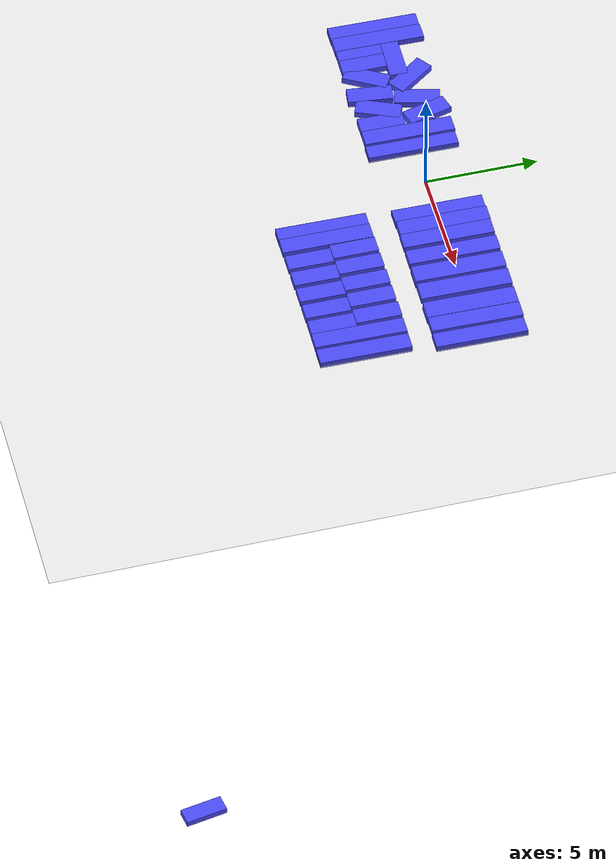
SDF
<sdf version="1.7">
 <world name="default">
  <light name="sun" type="directional">
   <pose>0 0 10 0 -0 0</pose>
   <diffuse>0.8 0.8 0.8 1</diffuse>
   <specular>0.2 0.2 0.2 1</specular>
   <attenuation>
    <range>1000</range>
    <constant>0.9</constant>
    <linear>0.01</linear>
    <quadratic>0.001</quadratic>
   </attenuation>
   <direction>-0.5 0.1 -0.9</direction>
   <spot><inner_angle>0</inner_angle><outer_angle>0</outer_angle><falloff>0</falloff></spot>
  </light>
  <model name="ground_plane">
   <static>1</static>
   <link name="link">
    <collision name="collision">
     <geometry><plane><normal>0 0 1</normal><size>100 100</size></plane></geometry>
     <surface><friction><ode><mu>100</mu><mu2>50</mu2></ode></friction></surface>
    </collision>
    <visual name="visual">
     <cast_shadows>0</cast_shadows>
     <geometry><plane><normal>0 0 1</normal><size>100 100</size></plane></geometry>
     <material>
      <script><uri>file://media/materials/scripts/gazebo.material</uri><name>Gazebo/Grey</name></script>
     </material>
    </visual>
   </link>
  </model>
  <gravity>0 0 -9.8</gravity>
  <magnetic_field>6e-06 2.3e-05 -4.2e-05</magnetic_field>
  <atmosphere type="adiabatic"/>
  <physics type="ode">
   <max_step_size>0.001</max_step_size>
   <real_time_factor>1</real_time_factor>
   <real_time_update_rate>1000</real_time_update_rate>
  </physics>
  <scene><ambient>0.4 0.4 0.4 1</ambient><background>0.7 0.7 0.7 1</background><shadows>1</shadows></scene>
  <spherical_coordinates>
   <surface_model>EARTH_WGS84</surface_model>
   <latitude_deg>0</latitude_deg>
   <longitude_deg>0</longitude_deg>
   <elevation>0</elevation>
   <heading_deg>0</heading_deg>
  </spherical_coordinates>
  <model name="ban_400_80_30">
   <link name="link">
    <inertial>
     <mass>1</mass>
     <inertia>
      <ixx>0.166667</ixx>
      <ixy>0</ixy>
      <ixz>0</ixz>
      <iyy>0.166667</iyy>
      <iyz>0</iyz>
      <izz>0.166667</izz>
     </inertia>
    </inertial>
    <visual name="visual">
     <geometry><box><size>4 0.8 0.3</size></box></geometry>
     <material>
      <script><name>Gazebo/Grey</name><uri>file://media/materials/scripts/gazebo.material</uri></script>
      <shader type="pixel"><normal_map>__default__</normal_map></shader>
      <ambient>0.3 0.3 1 1</ambient>
      <diffuse>0.7 0.7 0.7 1</diffuse>
      <specular>0.01 0.01 0.01 1</specular>
      <emissive>0 0 0 1</emissive>
     </material>
    </visual>
    <collision name="collision">
     <geometry><box><size>4 0.8 0.3</size></box></geometry>
     <surface>
      <friction>
       <ode><mu>1</mu><mu2>1</mu2><fdir1>0 0 0</fdir1><slip1>0</slip1><slip2>0</slip2></ode>
       <torsional>
        <coefficient>1</coefficient>
        <patch_radius>0</patch_radius>
        <surface_radius>0</surface_radius>
        <use_patch_radius>1</use_patch_radius>
        <ode><slip>0</slip></ode>
       </torsional>
      </friction>
      <bounce><restitution_coefficient>0</restitution_coefficient><threshold>1e+06</threshold></bounce>
      <contact>
       <collide_without_contact>0</collide_without_contact>
       <collide_without_contact_bitmask>1</collide_without_contact_bitmask>
       <collide_bitmask>1</collide_bitmask>
       <ode>
        <soft_cfm>0</soft_cfm>
        <soft_erp>0.2</soft_erp>
        <kp>1e+13</kp>
        <kd>1</kd>
        <max_vel>0.01</max_vel>
        <min_depth>0</min_depth>
       </ode>
       <bullet>
        <split_impulse>1</split_impulse>
        <split_impulse_penetration_threshold>-0.01</split_impulse_penetration_threshold>
        <soft_cfm>0</soft_cfm>
        <soft_erp>0.2</soft_erp>
        <kp>1e+13</kp>
        <kd>1</kd>
       </bullet>
      </contact>
     </surface>
    </collision>
   </link>
   <static>1</static>
   <pose>1.81049 0.102489 0 0 -0 1.55763</pose>
  </model>
  <model name="ban_400_80_30_clone">
   <link name="link">
    <inertial>
     <mass>1</mass>
     <inertia>
      <ixx>0.166667</ixx>
      <ixy>0</ixy>
      <ixz>0</ixz>
      <iyy>0.166667</iyy>
      <iyz>0</iyz>
      <izz>0.166667</izz>
     </inertia>
    </inertial>
    <visual name="visual">
     <geometry><box><size>4 0.8 0.3</size></box></geometry>
     <material>
      <script><name>Gazebo/Grey</name><uri>file://media/materials/scripts/gazebo.material</uri></script>
      <shader type="pixel"><normal_map>__default__</normal_map></shader>
      <ambient>0.3 0.3 1 1</ambient>
      <diffuse>0.7 0.7 0.7 1</diffuse>
      <specular>0.01 0.01 0.01 1</specular>
      <emissive>0 0 0 1</emissive>
     </material>
    </visual>
    <collision name="collision">
     <geometry><box><size>4 0.8 0.3</size></box></geometry>
     <surface>
      <friction>
       <ode><mu>1</mu><mu2>1</mu2><fdir1>0 0 0</fdir1><slip1>0</slip1><slip2>0</slip2></ode>
       <torsional>
        <coefficient>1</coefficient>
        <patch_radius>0</patch_radius>
        <surface_radius>0</surface_radius>
        <use_patch_radius>1</use_patch_radius>
        <ode><slip>0</slip></ode>
       </torsional>
      </friction>
      <bounce><restitution_coefficient>0</restitution_coefficient><threshold>1e+06</threshold></bounce>
      <contact>
       <collide_without_contact>0</collide_without_contact>
       <collide_without_contact_bitmask>1</collide_without_contact_bitmask>
       <collide_bitmask>1</collide_bitmask>
       <ode>
        <soft_cfm>0</soft_cfm>
        <soft_erp>0.2</soft_erp>
        <kp>1e+13</kp>
        <kd>1</kd>
        <max_vel>0.01</max_vel>
        <min_depth>0</min_depth>
       </ode>
       <bullet>
        <split_impulse>1</split_impulse>
        <split_impulse_penetration_threshold>-0.01</split_impulse_penetration_threshold>
        <soft_cfm>0</soft_cfm>
        <soft_erp>0.2</soft_erp>
        <kp>1e+13</kp>
        <kd>1</kd>
       </bullet>
      </contact>
     </surface>
    </collision>
   </link>
   <static>1</static>
   <pose>2.60692 0.093561 0.150704 0 -0 1.55763</pose>
  </model>
  <model name="ban_400_80_30_clone_clone">
   <link name="link">
    <inertial>
     <mass>1</mass>
     <inertia>
      <ixx>0.166667</ixx>
      <ixy>0</ixy>
      <ixz>0</ixz>
      <iyy>0.166667</iyy>
      <iyz>0</iyz>
      <izz>0.166667</izz>
     </inertia>
    </inertial>
    <visual name="visual">
     <geometry><box><size>4 0.8 0.3</size></box></geometry>
     <material>
      <script><name>Gazebo/Grey</name><uri>file://media/materials/scripts/gazebo.material</uri></script>
      <shader type="pixel"><normal_map>__default__</normal_map></shader>
      <ambient>0.3 0.3 1 1</ambient>
      <diffuse>0.7 0.7 0.7 1</diffuse>
      <specular>0.01 0.01 0.01 1</specular>
      <emissive>0 0 0 1</emissive>
     </material>
    </visual>
    <collision name="collision">
     <geometry><box><size>4 0.8 0.3</size></box></geometry>
     <surface>
      <friction>
       <ode><mu>1</mu><mu2>1</mu2><fdir1>0 0 0</fdir1><slip1>0</slip1><slip2>0</slip2></ode>
       <torsional>
        <coefficient>1</coefficient>
        <patch_radius>0</patch_radius>
        <surface_radius>0</surface_radius>
        <use_patch_radius>1</use_patch_radius>
        <ode><slip>0</slip></ode>
       </torsional>
      </friction>
      <bounce><restitution_coefficient>0</restitution_coefficient><threshold>1e+06</threshold></bounce>
      <contact>
       <collide_without_contact>0</collide_without_contact>
       <collide_without_contact_bitmask>1</collide_without_contact_bitmask>
       <collide_bitmask>1</collide_bitmask>
       <ode>
        <soft_cfm>0</soft_cfm>
        <soft_erp>0.2</soft_erp>
        <kp>1e+13</kp>
        <kd>1</kd>
        <max_vel>0.01</max_vel>
        <min_depth>0</min_depth>
       </ode>
       <bullet>
        <split_impulse>1</split_impulse>
        <split_impulse_penetration_threshold>-0.01</split_impulse_penetration_threshold>
        <soft_cfm>0</soft_cfm>
        <soft_erp>0.2</soft_erp>
        <kp>1e+13</kp>
        <kd>1</kd>
       </bullet>
      </contact>
     </surface>
    </collision>
   </link>
   <static>1</static>
   <pose>3.39245 0.063056 0.15556 0 -0 1.55763</pose>
  </model>
  <model name="ban_400_80_30_clone_clone_clone">
   <link name="link">
    <inertial>
     <mass>1</mass>
     <inertia>
      <ixx>0.166667</ixx>
      <ixy>0</ixy>
      <ixz>0</ixz>
      <iyy>0.166667</iyy>
      <iyz>0</iyz>
      <izz>0.166667</izz>
     </inertia>
    </inertial>
    <visual name="visual">
     <geometry><box><size>4 0.8 0.3</size></box></geometry>
     <material>
      <script><name>Gazebo/Grey</name><uri>file://media/materials/scripts/gazebo.material</uri></script>
      <shader type="pixel"><normal_map>__default__</normal_map></shader>
      <ambient>0.3 0.3 1 1</ambient>
      <diffuse>0.7 0.7 0.7 1</diffuse>
      <specular>0.01 0.01 0.01 1</specular>
      <emissive>0 0 0 1</emissive>
     </material>
    </visual>
    <collision name="collision">
     <geometry><box><size>4 0.8 0.3</size></box></geometry>
     <surface>
      <friction>
       <ode><mu>1</mu><mu2>1</mu2><fdir1>0 0 0</fdir1><slip1>0</slip1><slip2>0</slip2></ode>
       <torsional>
        <coefficient>1</coefficient>
        <patch_radius>0</patch_radius>
        <surface_radius>0</surface_radius>
        <use_patch_radius>1</use_patch_radius>
        <ode><slip>0</slip></ode>
       </torsional>
      </friction>
      <bounce><restitution_coefficient>0</restitution_coefficient><threshold>1e+06</threshold></bounce>
      <contact>
       <collide_without_contact>0</collide_without_contact>
       <collide_without_contact_bitmask>1</collide_without_contact_bitmask>
       <collide_bitmask>1</collide_bitmask>
       <ode>
        <soft_cfm>0</soft_cfm>
        <soft_erp>0.2</soft_erp>
        <kp>1e+13</kp>
        <kd>1</kd>
        <max_vel>0.01</max_vel>
        <min_depth>0</min_depth>
       </ode>
       <bullet>
        <split_impulse>1</split_impulse>
        <split_impulse_penetration_threshold>-0.01</split_impulse_penetration_threshold>
        <soft_cfm>0</soft_cfm>
        <soft_erp>0.2</soft_erp>
        <kp>1e+13</kp>
        <kd>1</kd>
       </bullet>
      </contact>
     </surface>
    </collision>
   </link>
   <static>1</static>
   <pose>4.37496 0.053031 0.15556 0 -0 1.55763</pose>
  </model>
  <model name="ban_400_80_30_clone_clone_clone_clone">
   <link name="link">
    <inertial>
     <mass>1</mass>
     <inertia>
      <ixx>0.166667</ixx>
      <ixy>0</ixy>
      <ixz>0</ixz>
      <iyy>0.166667</iyy>
      <iyz>0</iyz>
      <izz>0.166667</izz>
     </inertia>
    </inertial>
    <visual name="visual">
     <geometry><box><size>4 0.884488 0.419826</size></box></geometry>
     <material>
      <script><name>Gazebo/Grey</name><uri>file://media/materials/scripts/gazebo.material</uri></script>
      <shader type="pixel"><normal_map>__default__</normal_map></shader>
      <ambient>0.3 0.3 1 1</ambient>
      <diffuse>0.7 0.7 0.7 1</diffuse>
      <specular>0.01 0.01 0.01 1</specular>
      <emissive>0 0 0 1</emissive>
     </material>
    </visual>
    <collision name="collision">
     <geometry><box><size>4 0.884488 0.419826</size></box></geometry>
     <surface>
      <friction>
       <ode><mu>1</mu><mu2>1</mu2><fdir1>0 0 0</fdir1><slip1>0</slip1><slip2>0</slip2></ode>
       <torsional>
        <coefficient>1</coefficient>
        <patch_radius>0</patch_radius>
        <surface_radius>0</surface_radius>
        <use_patch_radius>1</use_patch_radius>
        <ode><slip>0</slip></ode>
       </torsional>
      </friction>
      <bounce><restitution_coefficient>0</restitution_coefficient><threshold>1e+06</threshold></bounce>
      <contact>
       <collide_without_contact>0</collide_without_contact>
       <collide_without_contact_bitmask>1</collide_without_contact_bitmask>
       <collide_bitmask>1</collide_bitmask>
       <ode>
        <soft_cfm>0</soft_cfm>
        <soft_erp>0.2</soft_erp>
        <kp>1e+13</kp>
        <kd>1</kd>
        <max_vel>0.01</max_vel>
        <min_depth>0</min_depth>
       </ode>
       <bullet>
        <split_impulse>1</split_impulse>
        <split_impulse_penetration_threshold>-0.01</split_impulse_penetration_threshold>
        <soft_cfm>0</soft_cfm>
        <soft_erp>0.2</soft_erp>
        <kp>1e+13</kp>
        <kd>1</kd>
       </bullet>
      </contact>
     </surface>
    </collision>
   </link>
   <static>1</static>
   <pose>5.36986 0.045316 0.097515 0 -0 1.55763</pose>
  </model>
  <model name="ban_400_80_30_clone_clone_clone_clone_0">
   <link name="link">
    <inertial>
     <mass>1</mass>
     <inertia>
      <ixx>0.166667</ixx>
      <ixy>0</ixy>
      <ixz>0</ixz>
      <iyy>0.166667</iyy>
      <iyz>0</iyz>
      <izz>0.166667</izz>
     </inertia>
    </inertial>
    <visual name="visual">
     <geometry><box><size>4 0.893808 0.3</size></box></geometry>
     <material>
      <script><name>Gazebo/Grey</name><uri>file://media/materials/scripts/gazebo.material</uri></script>
      <shader type="pixel"><normal_map>__default__</normal_map></shader>
      <ambient>0.3 0.3 1 1</ambient>
      <diffuse>0.7 0.7 0.7 1</diffuse>
      <specular>0.01 0.01 0.01 1</specular>
      <emissive>0 0 0 1</emissive>
     </material>
    </visual>
    <collision name="collision">
     <geometry><box><size>4 0.893808 0.3</size></box></geometry>
     <surface>
      <friction>
       <ode><mu>1</mu><mu2>1</mu2><fdir1>0 0 0</fdir1><slip1>0</slip1><slip2>0</slip2></ode>
       <torsional>
        <coefficient>1</coefficient>
        <patch_radius>0</patch_radius>
        <surface_radius>0</surface_radius>
        <use_patch_radius>1</use_patch_radius>
        <ode><slip>0</slip></ode>
       </torsional>
      </friction>
      <bounce><restitution_coefficient>0</restitution_coefficient><threshold>1e+06</threshold></bounce>
      <contact>
       <collide_without_contact>0</collide_without_contact>
       <collide_without_contact_bitmask>1</collide_without_contact_bitmask>
       <collide_bitmask>1</collide_bitmask>
       <ode>
        <soft_cfm>0</soft_cfm>
        <soft_erp>0.2</soft_erp>
        <kp>1e+13</kp>
        <kd>1</kd>
        <max_vel>0.01</max_vel>
        <min_depth>0</min_depth>
       </ode>
       <bullet>
        <split_impulse>1</split_impulse>
        <split_impulse_penetration_threshold>-0.01</split_impulse_penetration_threshold>
        <soft_cfm>0</soft_cfm>
        <soft_erp>0.2</soft_erp>
        <kp>1e+13</kp>
        <kd>1</kd>
       </bullet>
      </contact>
     </surface>
    </collision>
   </link>
   <static>1</static>
   <pose>6.39845 0.026417 0.15556 0 -0 1.55763</pose>
  </model>
  <model name="ban_400_80_30_clone_clone_clone_clone_clone">
   <link name="link">
    <inertial>
     <mass>1</mass>
     <inertia>
      <ixx>0.166667</ixx>
      <ixy>0</ixy>
      <ixz>0</ixz>
      <iyy>0.166667</iyy>
      <iyz>0</iyz>
      <izz>0.166667</izz>
     </inertia>
    </inertial>
    <visual name="visual">
     <geometry><box><size>4 0.884489 0.419826</size></box></geometry>
     <material>
      <script><name>Gazebo/Grey</name><uri>file://media/materials/scripts/gazebo.material</uri></script>
      <shader type="pixel"><normal_map>__default__</normal_map></shader>
      <ambient>0.3 0.3 1 1</ambient>
      <diffuse>0.7 0.7 0.7 1</diffuse>
      <specular>0.01 0.01 0.01 1</specular>
      <emissive>0 0 0 1</emissive>
     </material>
    </visual>
    <collision name="collision">
     <geometry><box><size>4 0.884489 0.419826</size></box></geometry>
     <surface>
      <friction>
       <ode><mu>1</mu><mu2>1</mu2><fdir1>0 0 0</fdir1><slip1>0</slip1><slip2>0</slip2></ode>
       <torsional>
        <coefficient>1</coefficient>
        <patch_radius>0</patch_radius>
        <surface_radius>0</surface_radius>
        <use_patch_radius>1</use_patch_radius>
        <ode><slip>0</slip></ode>
       </torsional>
      </friction>
      <bounce><restitution_coefficient>0</restitution_coefficient><threshold>1e+06</threshold></bounce>
      <contact>
       <collide_without_contact>0</collide_without_contact>
       <collide_without_contact_bitmask>1</collide_without_contact_bitmask>
       <collide_bitmask>1</collide_bitmask>
       <ode>
        <soft_cfm>0</soft_cfm>
        <soft_erp>0.2</soft_erp>
        <kp>1e+13</kp>
        <kd>1</kd>
        <max_vel>0.01</max_vel>
        <min_depth>0</min_depth>
       </ode>
       <bullet>
        <split_impulse>1</split_impulse>
        <split_impulse_penetration_threshold>-0.01</split_impulse_penetration_threshold>
        <soft_cfm>0</soft_cfm>
        <soft_erp>0.2</soft_erp>
        <kp>1e+13</kp>
        <kd>1</kd>
       </bullet>
      </contact>
     </surface>
    </collision>
   </link>
   <static>1</static>
   <pose>7.49306 0.005349 0.097515 0 -0 1.55763</pose>
  </model>
  <model name="ban_400_80_30_clone_clone_0">
   <link name="link">
    <inertial>
     <mass>1</mass>
     <inertia>
      <ixx>0.166667</ixx>
      <ixy>0</ixy>
      <ixz>0</ixz>
      <iyy>0.166667</iyy>
      <iyz>0</iyz>
      <izz>0.166667</izz>
     </inertia>
    </inertial>
    <visual name="visual">
     <geometry><box><size>4 0.8 0.3</size></box></geometry>
     <material>
      <script><name>Gazebo/Grey</name><uri>file://media/materials/scripts/gazebo.material</uri></script>
      <shader type="pixel"><normal_map>__default__</normal_map></shader>
      <ambient>0.3 0.3 1 1</ambient>
      <diffuse>0.7 0.7 0.7 1</diffuse>
      <specular>0.01 0.01 0.01 1</specular>
      <emissive>0 0 0 1</emissive>
     </material>
    </visual>
    <collision name="collision">
     <geometry><box><size>4 0.8 0.3</size></box></geometry>
     <surface>
      <friction>
       <ode><mu>1</mu><mu2>1</mu2><fdir1>0 0 0</fdir1><slip1>0</slip1><slip2>0</slip2></ode>
       <torsional>
        <coefficient>1</coefficient>
        <patch_radius>0</patch_radius>
        <surface_radius>0</surface_radius>
        <use_patch_radius>1</use_patch_radius>
        <ode><slip>0</slip></ode>
       </torsional>
      </friction>
      <bounce><restitution_coefficient>0</restitution_coefficient><threshold>1e+06</threshold></bounce>
      <contact>
       <collide_without_contact>0</collide_without_contact>
       <collide_without_contact_bitmask>1</collide_without_contact_bitmask>
       <collide_bitmask>1</collide_bitmask>
       <ode>
        <soft_cfm>0</soft_cfm>
        <soft_erp>0.2</soft_erp>
        <kp>1e+13</kp>
        <kd>1</kd>
        <max_vel>0.01</max_vel>
        <min_depth>0</min_depth>
       </ode>
       <bullet>
        <split_impulse>1</split_impulse>
        <split_impulse_penetration_threshold>-0.01</split_impulse_penetration_threshold>
        <soft_cfm>0</soft_cfm>
        <soft_erp>0.2</soft_erp>
        <kp>1e+13</kp>
        <kd>1</kd>
       </bullet>
      </contact>
     </surface>
    </collision>
   </link>
   <static>1</static>
   <pose>8.33888 -0.001923 0.150704 0 -0 1.55763</pose>
  </model>
  <model name="ban_400_80_30_clone_0">
   <link name="link">
    <inertial>
     <mass>1</mass>
     <inertia>
      <ixx>0.166667</ixx>
      <ixy>0</ixy>
      <ixz>0</ixz>
      <iyy>0.166667</iyy>
      <iyz>0</iyz>
      <izz>0.166667</izz>
     </inertia>
    </inertial>
    <visual name="visual">
     <geometry><box><size>4 0.8 0.3</size></box></geometry>
     <material>
      <script><name>Gazebo/Grey</name><uri>file://media/materials/scripts/gazebo.material</uri></script>
      <shader type="pixel"><normal_map>__default__</normal_map></shader>
      <ambient>0.3 0.3 1 1</ambient>
      <diffuse>0.7 0.7 0.7 1</diffuse>
      <specular>0.01 0.01 0.01 1</specular>
      <emissive>0 0 0 1</emissive>
     </material>
    </visual>
    <collision name="collision">
     <geometry><box><size>4 0.8 0.3</size></box></geometry>
     <surface>
      <friction>
       <ode><mu>1</mu><mu2>1</mu2><fdir1>0 0 0</fdir1><slip1>0</slip1><slip2>0</slip2></ode>
       <torsional>
        <coefficient>1</coefficient>
        <patch_radius>0</patch_radius>
        <surface_radius>0</surface_radius>
        <use_patch_radius>1</use_patch_radius>
        <ode><slip>0</slip></ode>
       </torsional>
      </friction>
      <bounce><restitution_coefficient>0</restitution_coefficient><threshold>1e+06</threshold></bounce>
      <contact>
       <collide_without_contact>0</collide_without_contact>
       <collide_without_contact_bitmask>1</collide_without_contact_bitmask>
       <collide_bitmask>1</collide_bitmask>
       <ode>
        <soft_cfm>0</soft_cfm>
        <soft_erp>0.2</soft_erp>
        <kp>1e+13</kp>
        <kd>1</kd>
        <max_vel>0.01</max_vel>
        <min_depth>0</min_depth>
       </ode>
       <bullet>
        <split_impulse>1</split_impulse>
        <split_impulse_penetration_threshold>-0.01</split_impulse_penetration_threshold>
        <soft_cfm>0</soft_cfm>
        <soft_erp>0.2</soft_erp>
        <kp>1e+13</kp>
        <kd>1</kd>
       </bullet>
      </contact>
     </surface>
    </collision>
   </link>
   <static>1</static>
   <pose>9.1293 -0.014354 0 0 -0 1.55763</pose>
  </model>
  <model name="ban_400_80_30_clone_1">
   <link name="link">
    <inertial>
     <mass>1</mass>
     <inertia>
      <ixx>0.166667</ixx>
      <ixy>0</ixy>
      <ixz>0</ixz>
      <iyy>0.166667</iyy>
      <iyz>0</iyz>
      <izz>0.166667</izz>
     </inertia>
    </inertial>
    <visual name="visual">
     <geometry><box><size>4 0.8 0.3</size></box></geometry>
     <material>
      <script><name>Gazebo/Grey</name><uri>file://media/materials/scripts/gazebo.material</uri></script>
      <shader type="pixel"><normal_map>__default__</normal_map></shader>
      <ambient>0.3 0.3 1 1</ambient>
      <diffuse>0.7 0.7 0.7 1</diffuse>
      <specular>0.01 0.01 0.01 1</specular>
      <emissive>0 0 0 1</emissive>
     </material>
    </visual>
    <collision name="collision">
     <geometry><box><size>4 0.8 0.3</size></box></geometry>
     <surface>
      <friction>
       <ode><mu>1</mu><mu2>1</mu2><fdir1>0 0 0</fdir1><slip1>0</slip1><slip2>0</slip2></ode>
       <torsional>
        <coefficient>1</coefficient>
        <patch_radius>0</patch_radius>
        <surface_radius>0</surface_radius>
        <use_patch_radius>1</use_patch_radius>
        <ode><slip>0</slip></ode>
       </torsional>
      </friction>
      <bounce><restitution_coefficient>0</restitution_coefficient><threshold>1e+06</threshold></bounce>
      <contact>
       <collide_without_contact>0</collide_without_contact>
       <collide_without_contact_bitmask>1</collide_without_contact_bitmask>
       <collide_bitmask>1</collide_bitmask>
       <ode>
        <soft_cfm>0</soft_cfm>
        <soft_erp>0.2</soft_erp>
        <kp>1e+13</kp>
        <kd>1</kd>
        <max_vel>0.01</max_vel>
        <min_depth>0</min_depth>
       </ode>
       <bullet>
        <split_impulse>1</split_impulse>
        <split_impulse_penetration_threshold>-0.01</split_impulse_penetration_threshold>
        <soft_cfm>0</soft_cfm>
        <soft_erp>0.2</soft_erp>
        <kp>1e+13</kp>
        <kd>1</kd>
       </bullet>
      </contact>
     </surface>
    </collision>
   </link>
   <static>1</static>
   <pose>1.61045 -5.009 0 0 -0 1.55763</pose>
  </model>
  <model name="ban_400_80_30_clone_2">
   <link name="link">
    <inertial>
     <mass>1</mass>
     <inertia>
      <ixx>0.166667</ixx>
      <ixy>0</ixy>
      <ixz>0</ixz>
      <iyy>0.166667</iyy>
      <iyz>0</iyz>
      <izz>0.166667</izz>
     </inertia>
    </inertial>
    <visual name="visual">
     <geometry><box><size>4 0.8 0.3</size></box></geometry>
     <material>
      <script><name>Gazebo/Grey</name><uri>file://media/materials/scripts/gazebo.material</uri></script>
      <shader type="pixel"><normal_map>__default__</normal_map></shader>
      <ambient>0.3 0.3 1 1</ambient>
      <diffuse>0.7 0.7 0.7 1</diffuse>
      <specular>0.01 0.01 0.01 1</specular>
      <emissive>0 0 0 1</emissive>
     </material>
    </visual>
    <collision name="collision">
     <geometry><box><size>4 0.8 0.3</size></box></geometry>
     <surface>
      <friction>
       <ode><mu>1</mu><mu2>1</mu2><fdir1>0 0 0</fdir1><slip1>0</slip1><slip2>0</slip2></ode>
       <torsional>
        <coefficient>1</coefficient>
        <patch_radius>0</patch_radius>
        <surface_radius>0</surface_radius>
        <use_patch_radius>1</use_patch_radius>
        <ode><slip>0</slip></ode>
       </torsional>
      </friction>
      <bounce><restitution_coefficient>0</restitution_coefficient><threshold>1e+06</threshold></bounce>
      <contact>
       <collide_without_contact>0</collide_without_contact>
       <collide_without_contact_bitmask>1</collide_without_contact_bitmask>
       <collide_bitmask>1</collide_bitmask>
       <ode>
        <soft_cfm>0</soft_cfm>
        <soft_erp>0.2</soft_erp>
        <kp>1e+13</kp>
        <kd>1</kd>
        <max_vel>0.01</max_vel>
        <min_depth>0</min_depth>
       </ode>
       <bullet>
        <split_impulse>1</split_impulse>
        <split_impulse_penetration_threshold>-0.01</split_impulse_penetration_threshold>
        <soft_cfm>0</soft_cfm>
        <soft_erp>0.2</soft_erp>
        <kp>1e+13</kp>
        <kd>1</kd>
       </bullet>
      </contact>
     </surface>
    </collision>
   </link>
   <static>1</static>
   <pose>2.36163 -5.0304 0.12761 0 -0 1.56189</pose>
  </model>
  <model name="ban_200_80_30">
   <link name="link">
    <inertial>
     <mass>1</mass>
     <inertia>
      <ixx>0.166667</ixx>
      <ixy>0</ixy>
      <ixz>0</ixz>
      <iyy>0.166667</iyy>
      <iyz>0</iyz>
      <izz>0.166667</izz>
     </inertia>
    </inertial>
    <visual name="visual">
     <geometry><box><size>2 0.8 0.3</size></box></geometry>
     <material>
      <script><name>Gazebo/Grey</name><uri>file://media/materials/scripts/gazebo.material</uri></script>
      <shader type="pixel"><normal_map>__default__</normal_map></shader>
      <ambient>0.3 0.3 1 1</ambient>
      <diffuse>0.7 0.7 0.7 1</diffuse>
      <specular>0.01 0.01 0.01 1</specular>
      <emissive>0 0 0 1</emissive>
     </material>
    </visual>
    <collision name="collision">
     <geometry><box><size>2 0.8 0.3</size></box></geometry>
     <surface>
      <friction>
       <ode><mu>1</mu><mu2>1</mu2><fdir1>0 0 0</fdir1><slip1>0</slip1><slip2>0</slip2></ode>
       <torsional>
        <coefficient>1</coefficient>
        <patch_radius>0</patch_radius>
        <surface_radius>0</surface_radius>
        <use_patch_radius>1</use_patch_radius>
        <ode><slip>0</slip></ode>
       </torsional>
      </friction>
      <bounce><restitution_coefficient>0</restitution_coefficient><threshold>1e+06</threshold></bounce>
      <contact>
       <collide_without_contact>0</collide_without_contact>
       <collide_without_contact_bitmask>1</collide_without_contact_bitmask>
       <collide_bitmask>1</collide_bitmask>
       <ode>
        <soft_cfm>0</soft_cfm>
        <soft_erp>0.2</soft_erp>
        <kp>1e+13</kp>
        <kd>1</kd>
        <max_vel>0.01</max_vel>
        <min_depth>0</min_depth>
       </ode>
       <bullet>
        <split_impulse>1</split_impulse>
        <split_impulse_penetration_threshold>-0.01</split_impulse_penetration_threshold>
        <soft_cfm>0</soft_cfm>
        <soft_erp>0.2</soft_erp>
        <kp>1e+13</kp>
        <kd>1</kd>
       </bullet>
      </contact>
     </surface>
    </collision>
   </link>
   <static>1</static>
   <pose>3.19073 -4.01387 0.12138 0 0 -1.57453</pose>
  </model>
  <model name="ban_200_80_30_clone">
   <link name="link">
    <inertial>
     <mass>1</mass>
     <inertia>
      <ixx>0.166667</ixx>
      <ixy>0</ixy>
      <ixz>0</ixz>
      <iyy>0.166667</iyy>
      <iyz>0</iyz>
      <izz>0.166667</izz>
     </inertia>
    </inertial>
    <visual name="visual">
     <geometry><box><size>2 0.8 0.3</size></box></geometry>
     <material>
      <script><name>Gazebo/Grey</name><uri>file://media/materials/scripts/gazebo.material</uri></script>
      <shader type="pixel"><normal_map>__default__</normal_map></shader>
      <ambient>0.3 0.3 1 1</ambient>
      <diffuse>0.7 0.7 0.7 1</diffuse>
      <specular>0.01 0.01 0.01 1</specular>
      <emissive>0 0 0 1</emissive>
     </material>
    </visual>
    <collision name="collision">
     <geometry><box><size>2 0.8 0.3</size></box></geometry>
     <surface>
      <friction>
       <ode><mu>1</mu><mu2>1</mu2><fdir1>0 0 0</fdir1><slip1>0</slip1><slip2>0</slip2></ode>
       <torsional>
        <coefficient>1</coefficient>
        <patch_radius>0</patch_radius>
        <surface_radius>0</surface_radius>
        <use_patch_radius>1</use_patch_radius>
        <ode><slip>0</slip></ode>
       </torsional>
      </friction>
      <bounce><restitution_coefficient>0</restitution_coefficient><threshold>1e+06</threshold></bounce>
      <contact>
       <collide_without_contact>0</collide_without_contact>
       <collide_without_contact_bitmask>1</collide_without_contact_bitmask>
       <collide_bitmask>1</collide_bitmask>
       <ode>
        <soft_cfm>0</soft_cfm>
        <soft_erp>0.2</soft_erp>
        <kp>1e+13</kp>
        <kd>1</kd>
        <max_vel>0.01</max_vel>
        <min_depth>0</min_depth>
       </ode>
       <bullet>
        <split_impulse>1</split_impulse>
        <split_impulse_penetration_threshold>-0.01</split_impulse_penetration_threshold>
        <soft_cfm>0</soft_cfm>
        <soft_erp>0.2</soft_erp>
        <kp>1e+13</kp>
        <kd>1</kd>
       </bullet>
      </contact>
     </surface>
    </collision>
   </link>
   <static>1</static>
   <pose>3.34228 -6.01948 0.12138 0 0 -1.57453</pose>
  </model>
  <model name="ban_200_80_30_clone_0">
   <link name="link">
    <inertial>
     <mass>1</mass>
     <inertia>
      <ixx>0.166667</ixx>
      <ixy>0</ixy>
      <ixz>0</ixz>
      <iyy>0.166667</iyy>
      <iyz>0</iyz>
      <izz>0.166667</izz>
     </inertia>
    </inertial>
    <visual name="visual">
     <geometry><box><size>2 0.8 0.3</size></box></geometry>
     <material>
      <script><name>Gazebo/Grey</name><uri>file://media/materials/scripts/gazebo.material</uri></script>
      <shader type="pixel"><normal_map>__default__</normal_map></shader>
      <ambient>0.3 0.3 1 1</ambient>
      <diffuse>0.7 0.7 0.7 1</diffuse>
      <specular>0.01 0.01 0.01 1</specular>
      <emissive>0 0 0 1</emissive>
     </material>
    </visual>
    <collision name="collision">
     <geometry><box><size>2 0.8 0.3</size></box></geometry>
     <surface>
      <friction>
       <ode><mu>1</mu><mu2>1</mu2><fdir1>0 0 0</fdir1><slip1>0</slip1><slip2>0</slip2></ode>
       <torsional>
        <coefficient>1</coefficient>
        <patch_radius>0</patch_radius>
        <surface_radius>0</surface_radius>
        <use_patch_radius>1</use_patch_radius>
        <ode><slip>0</slip></ode>
       </torsional>
      </friction>
      <bounce><restitution_coefficient>0</restitution_coefficient><threshold>1e+06</threshold></bounce>
      <contact>
       <collide_without_contact>0</collide_without_contact>
       <collide_without_contact_bitmask>1</collide_without_contact_bitmask>
       <collide_bitmask>1</collide_bitmask>
       <ode>
        <soft_cfm>0</soft_cfm>
        <soft_erp>0.2</soft_erp>
        <kp>1e+13</kp>
        <kd>1</kd>
        <max_vel>0.01</max_vel>
        <min_depth>0</min_depth>
       </ode>
       <bullet>
        <split_impulse>1</split_impulse>
        <split_impulse_penetration_threshold>-0.01</split_impulse_penetration_threshold>
        <soft_cfm>0</soft_cfm>
        <soft_erp>0.2</soft_erp>
        <kp>1e+13</kp>
        <kd>1</kd>
       </bullet>
      </contact>
     </surface>
    </collision>
   </link>
   <static>1</static>
   <pose>4.13438 -4.00905 0.12138 0 0 -1.57453</pose>
  </model>
  <model name="ban_200_80_30_clone_1">
   <link name="link">
    <inertial>
     <mass>1</mass>
     <inertia>
      <ixx>0.166667</ixx>
      <ixy>0</ixy>
      <ixz>0</ixz>
      <iyy>0.166667</iyy>
      <iyz>0</iyz>
      <izz>0.166667</izz>
     </inertia>
    </inertial>
    <visual name="visual">
     <geometry><box><size>2 0.8 0.3</size></box></geometry>
     <material>
      <script><name>Gazebo/Grey</name><uri>file://media/materials/scripts/gazebo.material</uri></script>
      <shader type="pixel"><normal_map>__default__</normal_map></shader>
      <ambient>0.3 0.3 1 1</ambient>
      <diffuse>0.7 0.7 0.7 1</diffuse>
      <specular>0.01 0.01 0.01 1</specular>
      <emissive>0 0 0 1</emissive>
     </material>
    </visual>
    <collision name="collision">
     <geometry><box><size>2 0.8 0.3</size></box></geometry>
     <surface>
      <friction>
       <ode><mu>1</mu><mu2>1</mu2><fdir1>0 0 0</fdir1><slip1>0</slip1><slip2>0</slip2></ode>
       <torsional>
        <coefficient>1</coefficient>
        <patch_radius>0</patch_radius>
        <surface_radius>0</surface_radius>
        <use_patch_radius>1</use_patch_radius>
        <ode><slip>0</slip></ode>
       </torsional>
      </friction>
      <bounce><restitution_coefficient>0</restitution_coefficient><threshold>1e+06</threshold></bounce>
      <contact>
       <collide_without_contact>0</collide_without_contact>
       <collide_without_contact_bitmask>1</collide_without_contact_bitmask>
       <collide_bitmask>1</collide_bitmask>
       <ode>
        <soft_cfm>0</soft_cfm>
        <soft_erp>0.2</soft_erp>
        <kp>1e+13</kp>
        <kd>1</kd>
        <max_vel>0.01</max_vel>
        <min_depth>0</min_depth>
       </ode>
       <bullet>
        <split_impulse>1</split_impulse>
        <split_impulse_penetration_threshold>-0.01</split_impulse_penetration_threshold>
        <soft_cfm>0</soft_cfm>
        <soft_erp>0.2</soft_erp>
        <kp>1e+13</kp>
        <kd>1</kd>
       </bullet>
      </contact>
     </surface>
    </collision>
   </link>
   <static>1</static>
   <pose>4.30573 -6.01081 0.12138 0 0 -1.57453</pose>
  </model>
  <model name="ban_200_80_30_clone_2">
   <link name="link">
    <inertial>
     <mass>1</mass>
     <inertia>
      <ixx>0.166667</ixx>
      <ixy>0</ixy>
      <ixz>0</ixz>
      <iyy>0.166667</iyy>
      <iyz>0</iyz>
      <izz>0.166667</izz>
     </inertia>
    </inertial>
    <visual name="visual">
     <geometry><box><size>2 0.8 0.3</size></box></geometry>
     <material>
      <script><name>Gazebo/Grey</name><uri>file://media/materials/scripts/gazebo.material</uri></script>
      <shader type="pixel"><normal_map>__default__</normal_map></shader>
      <ambient>0.3 0.3 1 1</ambient>
      <diffuse>0.7 0.7 0.7 1</diffuse>
      <specular>0.01 0.01 0.01 1</specular>
      <emissive>0 0 0 1</emissive>
     </material>
    </visual>
    <collision name="collision">
     <geometry><box><size>2 0.8 0.3</size></box></geometry>
     <surface>
      <friction>
       <ode><mu>1</mu><mu2>1</mu2><fdir1>0 0 0</fdir1><slip1>0</slip1><slip2>0</slip2></ode>
       <torsional>
        <coefficient>1</coefficient>
        <patch_radius>0</patch_radius>
        <surface_radius>0</surface_radius>
        <use_patch_radius>1</use_patch_radius>
        <ode><slip>0</slip></ode>
       </torsional>
      </friction>
      <bounce><restitution_coefficient>0</restitution_coefficient><threshold>1e+06</threshold></bounce>
      <contact>
       <collide_without_contact>0</collide_without_contact>
       <collide_without_contact_bitmask>1</collide_without_contact_bitmask>
       <collide_bitmask>1</collide_bitmask>
       <ode>
        <soft_cfm>0</soft_cfm>
        <soft_erp>0.2</soft_erp>
        <kp>1e+13</kp>
        <kd>1</kd>
        <max_vel>0.01</max_vel>
        <min_depth>0</min_depth>
       </ode>
       <bullet>
        <split_impulse>1</split_impulse>
        <split_impulse_penetration_threshold>-0.01</split_impulse_penetration_threshold>
        <soft_cfm>0</soft_cfm>
        <soft_erp>0.2</soft_erp>
        <kp>1e+13</kp>
        <kd>1</kd>
       </bullet>
      </contact>
     </surface>
    </collision>
   </link>
   <static>1</static>
   <pose>5.11893 -4.00066 0.12138 0 0 -1.57453</pose>
  </model>
  <model name="ban_200_80_30_clone_3">
   <link name="link">
    <inertial>
     <mass>1</mass>
     <inertia>
      <ixx>0.166667</ixx>
      <ixy>0</ixy>
      <ixz>0</ixz>
      <iyy>0.166667</iyy>
      <iyz>0</iyz>
      <izz>0.166667</izz>
     </inertia>
    </inertial>
    <visual name="visual">
     <geometry><box><size>2 0.8 0.3</size></box></geometry>
     <material>
      <script><name>Gazebo/Grey</name><uri>file://media/materials/scripts/gazebo.material</uri></script>
      <shader type="pixel"><normal_map>__default__</normal_map></shader>
      <ambient>0.3 0.3 1 1</ambient>
      <diffuse>0.7 0.7 0.7 1</diffuse>
      <specular>0.01 0.01 0.01 1</specular>
      <emissive>0 0 0 1</emissive>
     </material>
    </visual>
    <collision name="collision">
     <geometry><box><size>2 0.8 0.3</size></box></geometry>
     <surface>
      <friction>
       <ode><mu>1</mu><mu2>1</mu2><fdir1>0 0 0</fdir1><slip1>0</slip1><slip2>0</slip2></ode>
       <torsional>
        <coefficient>1</coefficient>
        <patch_radius>0</patch_radius>
        <surface_radius>0</surface_radius>
        <use_patch_radius>1</use_patch_radius>
        <ode><slip>0</slip></ode>
       </torsional>
      </friction>
      <bounce><restitution_coefficient>0</restitution_coefficient><threshold>1e+06</threshold></bounce>
      <contact>
       <collide_without_contact>0</collide_without_contact>
       <collide_without_contact_bitmask>1</collide_without_contact_bitmask>
       <collide_bitmask>1</collide_bitmask>
       <ode>
        <soft_cfm>0</soft_cfm>
        <soft_erp>0.2</soft_erp>
        <kp>1e+13</kp>
        <kd>1</kd>
        <max_vel>0.01</max_vel>
        <min_depth>0</min_depth>
       </ode>
       <bullet>
        <split_impulse>1</split_impulse>
        <split_impulse_penetration_threshold>-0.01</split_impulse_penetration_threshold>
        <soft_cfm>0</soft_cfm>
        <soft_erp>0.2</soft_erp>
        <kp>1e+13</kp>
        <kd>1</kd>
       </bullet>
      </contact>
     </surface>
    </collision>
   </link>
   <static>1</static>
   <pose>5.28348 -6.00227 0.12138 0 0 -1.57453</pose>
  </model>
  <model name="ban_200_80_30_clone_4">
   <link name="link">
    <inertial>
     <mass>1</mass>
     <inertia>
      <ixx>0.166667</ixx>
      <ixy>0</ixy>
      <ixz>0</ixz>
      <iyy>0.166667</iyy>
      <iyz>0</iyz>
      <izz>0.166667</izz>
     </inertia>
    </inertial>
    <visual name="visual">
     <geometry><box><size>2 0.8 0.3</size></box></geometry>
     <material>
      <script><name>Gazebo/Grey</name><uri>file://media/materials/scripts/gazebo.material</uri></script>
      <shader type="pixel"><normal_map>__default__</normal_map></shader>
      <ambient>0.3 0.3 1 1</ambient>
      <diffuse>0.7 0.7 0.7 1</diffuse>
      <specular>0.01 0.01 0.01 1</specular>
      <emissive>0 0 0 1</emissive>
     </material>
    </visual>
    <collision name="collision">
     <geometry><box><size>2 0.8 0.3</size></box></geometry>
     <surface>
      <friction>
       <ode><mu>1</mu><mu2>1</mu2><fdir1>0 0 0</fdir1><slip1>0</slip1><slip2>0</slip2></ode>
       <torsional>
        <coefficient>1</coefficient>
        <patch_radius>0</patch_radius>
        <surface_radius>0</surface_radius>
        <use_patch_radius>1</use_patch_radius>
        <ode><slip>0</slip></ode>
       </torsional>
      </friction>
      <bounce><restitution_coefficient>0</restitution_coefficient><threshold>1e+06</threshold></bounce>
      <contact>
       <collide_without_contact>0</collide_without_contact>
       <collide_without_contact_bitmask>1</collide_without_contact_bitmask>
       <collide_bitmask>1</collide_bitmask>
       <ode>
        <soft_cfm>0</soft_cfm>
        <soft_erp>0.2</soft_erp>
        <kp>1e+13</kp>
        <kd>1</kd>
        <max_vel>0.01</max_vel>
        <min_depth>0</min_depth>
       </ode>
       <bullet>
        <split_impulse>1</split_impulse>
        <split_impulse_penetration_threshold>-0.01</split_impulse_penetration_threshold>
        <soft_cfm>0</soft_cfm>
        <soft_erp>0.2</soft_erp>
        <kp>1e+13</kp>
        <kd>1</kd>
       </bullet>
      </contact>
     </surface>
    </collision>
   </link>
   <static>1</static>
   <pose>6.0825 -4.00246 0.12138 0 0 -1.57453</pose>
  </model>
  <model name="ban_200_80_30_clone_5">
   <link name="link">
    <inertial>
     <mass>1</mass>
     <inertia>
      <ixx>0.166667</ixx>
      <ixy>0</ixy>
      <ixz>0</ixz>
      <iyy>0.166667</iyy>
      <iyz>0</iyz>
      <izz>0.166667</izz>
     </inertia>
    </inertial>
    <visual name="visual">
     <geometry><box><size>2 0.8 0.3</size></box></geometry>
     <material>
      <script><name>Gazebo/Grey</name><uri>file://media/materials/scripts/gazebo.material</uri></script>
      <shader type="pixel"><normal_map>__default__</normal_map></shader>
      <ambient>0.3 0.3 1 1</ambient>
      <diffuse>0.7 0.7 0.7 1</diffuse>
      <specular>0.01 0.01 0.01 1</specular>
      <emissive>0 0 0 1</emissive>
     </material>
    </visual>
    <collision name="collision">
     <geometry><box><size>2 0.8 0.3</size></box></geometry>
     <surface>
      <friction>
       <ode><mu>1</mu><mu2>1</mu2><fdir1>0 0 0</fdir1><slip1>0</slip1><slip2>0</slip2></ode>
       <torsional>
        <coefficient>1</coefficient>
        <patch_radius>0</patch_radius>
        <surface_radius>0</surface_radius>
        <use_patch_radius>1</use_patch_radius>
        <ode><slip>0</slip></ode>
       </torsional>
      </friction>
      <bounce><restitution_coefficient>0</restitution_coefficient><threshold>1e+06</threshold></bounce>
      <contact>
       <collide_without_contact>0</collide_without_contact>
       <collide_without_contact_bitmask>1</collide_without_contact_bitmask>
       <collide_bitmask>1</collide_bitmask>
       <ode>
        <soft_cfm>0</soft_cfm>
        <soft_erp>0.2</soft_erp>
        <kp>1e+13</kp>
        <kd>1</kd>
        <max_vel>0.01</max_vel>
        <min_depth>0</min_depth>
       </ode>
       <bullet>
        <split_impulse>1</split_impulse>
        <split_impulse_penetration_threshold>-0.01</split_impulse_penetration_threshold>
        <soft_cfm>0</soft_cfm>
        <soft_erp>0.2</soft_erp>
        <kp>1e+13</kp>
        <kd>1</kd>
       </bullet>
      </contact>
     </surface>
    </collision>
   </link>
   <static>1</static>
   <pose>6.2591 -6.00201 0.12138 0 0 -1.57453</pose>
  </model>
  <model name="ban_200_80_30_clone_6">
   <link name="link">
    <inertial>
     <mass>1</mass>
     <inertia>
      <ixx>0.166667</ixx>
      <ixy>0</ixy>
      <ixz>0</ixz>
      <iyy>0.166667</iyy>
      <iyz>0</iyz>
      <izz>0.166667</izz>
     </inertia>
    </inertial>
    <visual name="visual">
     <geometry><box><size>2 0.8 0.3</size></box></geometry>
     <material>
      <script><name>Gazebo/Grey</name><uri>file://media/materials/scripts/gazebo.material</uri></script>
      <shader type="pixel"><normal_map>__default__</normal_map></shader>
      <ambient>0.3 0.3 1 1</ambient>
      <diffuse>0.7 0.7 0.7 1</diffuse>
      <specular>0.01 0.01 0.01 1</specular>
      <emissive>0 0 0 1</emissive>
     </material>
    </visual>
    <collision name="collision">
     <geometry><box><size>2 0.8 0.3</size></box></geometry>
     <surface>
      <friction>
       <ode><mu>1</mu><mu2>1</mu2><fdir1>0 0 0</fdir1><slip1>0</slip1><slip2>0</slip2></ode>
       <torsional>
        <coefficient>1</coefficient>
        <patch_radius>0</patch_radius>
        <surface_radius>0</surface_radius>
        <use_patch_radius>1</use_patch_radius>
        <ode><slip>0</slip></ode>
       </torsional>
      </friction>
      <bounce><restitution_coefficient>0</restitution_coefficient><threshold>1e+06</threshold></bounce>
      <contact>
       <collide_without_contact>0</collide_without_contact>
       <collide_without_contact_bitmask>1</collide_without_contact_bitmask>
       <collide_bitmask>1</collide_bitmask>
       <ode>
        <soft_cfm>0</soft_cfm>
        <soft_erp>0.2</soft_erp>
        <kp>1e+13</kp>
        <kd>1</kd>
        <max_vel>0.01</max_vel>
        <min_depth>0</min_depth>
       </ode>
       <bullet>
        <split_impulse>1</split_impulse>
        <split_impulse_penetration_threshold>-0.01</split_impulse_penetration_threshold>
        <soft_cfm>0</soft_cfm>
        <soft_erp>0.2</soft_erp>
        <kp>1e+13</kp>
        <kd>1</kd>
       </bullet>
      </contact>
     </surface>
    </collision>
   </link>
   <static>1</static>
   <pose>7.04749 -3.99179 0.12138 0 0 -1.57453</pose>
  </model>
  <model name="ban_200_80_30_clone_7">
   <link name="link">
    <inertial>
     <mass>1</mass>
     <inertia>
      <ixx>0.166667</ixx>
      <ixy>0</ixy>
      <ixz>0</ixz>
      <iyy>0.166667</iyy>
      <iyz>0</iyz>
      <izz>0.166667</izz>
     </inertia>
    </inertial>
    <visual name="visual">
     <geometry><box><size>2 0.8 0.3</size></box></geometry>
     <material>
      <script><name>Gazebo/Grey</name><uri>file://media/materials/scripts/gazebo.material</uri></script>
      <shader type="pixel"><normal_map>__default__</normal_map></shader>
      <ambient>0.3 0.3 1 1</ambient>
      <diffuse>0.7 0.7 0.7 1</diffuse>
      <specular>0.01 0.01 0.01 1</specular>
      <emissive>0 0 0 1</emissive>
     </material>
    </visual>
    <collision name="collision">
     <geometry><box><size>2 0.8 0.3</size></box></geometry>
     <surface>
      <friction>
       <ode><mu>1</mu><mu2>1</mu2><fdir1>0 0 0</fdir1><slip1>0</slip1><slip2>0</slip2></ode>
       <torsional>
        <coefficient>1</coefficient>
        <patch_radius>0</patch_radius>
        <surface_radius>0</surface_radius>
        <use_patch_radius>1</use_patch_radius>
        <ode><slip>0</slip></ode>
       </torsional>
      </friction>
      <bounce><restitution_coefficient>0</restitution_coefficient><threshold>1e+06</threshold></bounce>
      <contact>
       <collide_without_contact>0</collide_without_contact>
       <collide_without_contact_bitmask>1</collide_without_contact_bitmask>
       <collide_bitmask>1</collide_bitmask>
       <ode>
        <soft_cfm>0</soft_cfm>
        <soft_erp>0.2</soft_erp>
        <kp>1e+13</kp>
        <kd>1</kd>
        <max_vel>0.01</max_vel>
        <min_depth>0</min_depth>
       </ode>
       <bullet>
        <split_impulse>1</split_impulse>
        <split_impulse_penetration_threshold>-0.01</split_impulse_penetration_threshold>
        <soft_cfm>0</soft_cfm>
        <soft_erp>0.2</soft_erp>
        <kp>1e+13</kp>
        <kd>1</kd>
       </bullet>
      </contact>
     </surface>
    </collision>
   </link>
   <static>1</static>
   <pose>7.20156 -5.99933 0.12138 0 0 -1.57453</pose>
  </model>
  <model name="ban_400_80_30_clone_2_clone">
   <link name="link">
    <inertial>
     <mass>1</mass>
     <inertia>
      <ixx>0.166667</ixx>
      <ixy>0</ixy>
      <ixz>0</ixz>
      <iyy>0.166667</iyy>
      <iyz>0</iyz>
      <izz>0.166667</izz>
     </inertia>
    </inertial>
    <visual name="visual">
     <geometry><box><size>4 0.8 0.3</size></box></geometry>
     <material>
      <script><name>Gazebo/Grey</name><uri>file://media/materials/scripts/gazebo.material</uri></script>
      <shader type="pixel"><normal_map>__default__</normal_map></shader>
      <ambient>0.3 0.3 1 1</ambient>
      <diffuse>0.7 0.7 0.7 1</diffuse>
      <specular>0.01 0.01 0.01 1</specular>
      <emissive>0 0 0 1</emissive>
     </material>
    </visual>
    <collision name="collision">
     <geometry><box><size>4 0.8 0.3</size></box></geometry>
     <surface>
      <friction>
       <ode><mu>1</mu><mu2>1</mu2><fdir1>0 0 0</fdir1><slip1>0</slip1><slip2>0</slip2></ode>
       <torsional>
        <coefficient>1</coefficient>
        <patch_radius>0</patch_radius>
        <surface_radius>0</surface_radius>
        <use_patch_radius>1</use_patch_radius>
        <ode><slip>0</slip></ode>
       </torsional>
      </friction>
      <bounce><restitution_coefficient>0</restitution_coefficient><threshold>1e+06</threshold></bounce>
      <contact>
       <collide_without_contact>0</collide_without_contact>
       <collide_without_contact_bitmask>1</collide_without_contact_bitmask>
       <collide_bitmask>1</collide_bitmask>
       <ode>
        <soft_cfm>0</soft_cfm>
        <soft_erp>0.2</soft_erp>
        <kp>1e+13</kp>
        <kd>1</kd>
        <max_vel>0.01</max_vel>
        <min_depth>0</min_depth>
       </ode>
       <bullet>
        <split_impulse>1</split_impulse>
        <split_impulse_penetration_threshold>-0.01</split_impulse_penetration_threshold>
        <soft_cfm>0</soft_cfm>
        <soft_erp>0.2</soft_erp>
        <kp>1e+13</kp>
        <kd>1</kd>
       </bullet>
      </contact>
     </surface>
    </collision>
   </link>
   <static>1</static>
   <pose>7.98824 -5.01588 0.12761 0 -0 1.55763</pose>
  </model>
  <model name="ban_400_80_30_clone_1_clone">
   <link name="link">
    <inertial>
     <mass>1</mass>
     <inertia>
      <ixx>0.166667</ixx>
      <ixy>0</ixy>
      <ixz>0</ixz>
      <iyy>0.166667</iyy>
      <iyz>0</iyz>
      <izz>0.166667</izz>
     </inertia>
    </inertial>
    <visual name="visual">
     <geometry><box><size>4 0.8 0.3</size></box></geometry>
     <material>
      <script><name>Gazebo/Grey</name><uri>file://media/materials/scripts/gazebo.material</uri></script>
      <shader type="pixel"><normal_map>__default__</normal_map></shader>
      <ambient>0.3 0.3 1 1</ambient>
      <diffuse>0.7 0.7 0.7 1</diffuse>
      <specular>0.01 0.01 0.01 1</specular>
      <emissive>0 0 0 1</emissive>
     </material>
    </visual>
    <collision name="collision">
     <geometry><box><size>4 0.8 0.3</size></box></geometry>
     <surface>
      <friction>
       <ode><mu>1</mu><mu2>1</mu2><fdir1>0 0 0</fdir1><slip1>0</slip1><slip2>0</slip2></ode>
       <torsional>
        <coefficient>1</coefficient>
        <patch_radius>0</patch_radius>
        <surface_radius>0</surface_radius>
        <use_patch_radius>1</use_patch_radius>
        <ode><slip>0</slip></ode>
       </torsional>
      </friction>
      <bounce><restitution_coefficient>0</restitution_coefficient><threshold>1e+06</threshold></bounce>
      <contact>
       <collide_without_contact>0</collide_without_contact>
       <collide_without_contact_bitmask>1</collide_without_contact_bitmask>
       <collide_bitmask>1</collide_bitmask>
       <ode>
        <soft_cfm>0</soft_cfm>
        <soft_erp>0.2</soft_erp>
        <kp>1e+13</kp>
        <kd>1</kd>
        <max_vel>0.01</max_vel>
        <min_depth>0</min_depth>
       </ode>
       <bullet>
        <split_impulse>1</split_impulse>
        <split_impulse_penetration_threshold>-0.01</split_impulse_penetration_threshold>
        <soft_cfm>0</soft_cfm>
        <soft_erp>0.2</soft_erp>
        <kp>1e+13</kp>
        <kd>1</kd>
       </bullet>
      </contact>
     </surface>
    </collision>
   </link>
   <static>1</static>
   <pose>8.7964 -5.00772 0 0 -0 1.55763</pose>
  </model>
  <model name="ban_400_80_30_clone_1_clone_0">
   <link name="link">
    <inertial>
     <mass>1</mass>
     <inertia>
      <ixx>0.166667</ixx>
      <ixy>0</ixy>
      <ixz>0</ixz>
      <iyy>0.166667</iyy>
      <iyz>0</iyz>
      <izz>0.166667</izz>
     </inertia>
    </inertial>
    <visual name="visual">
     <geometry><box><size>4 0.8 0.3</size></box></geometry>
     <material>
      <script><name>Gazebo/Grey</name><uri>file://media/materials/scripts/gazebo.material</uri></script>
      <shader type="pixel"><normal_map>__default__</normal_map></shader>
      <ambient>0.3 0.3 1 1</ambient>
      <diffuse>0.7 0.7 0.7 1</diffuse>
      <specular>0.01 0.01 0.01 1</specular>
      <emissive>0 0 0 1</emissive>
     </material>
    </visual>
    <collision name="collision">
     <geometry><box><size>4 0.8 0.3</size></box></geometry>
     <surface>
      <friction>
       <ode><mu>1</mu><mu2>1</mu2><fdir1>0 0 0</fdir1><slip1>0</slip1><slip2>0</slip2></ode>
       <torsional>
        <coefficient>1</coefficient>
        <patch_radius>0</patch_radius>
        <surface_radius>0</surface_radius>
        <use_patch_radius>1</use_patch_radius>
        <ode><slip>0</slip></ode>
       </torsional>
      </friction>
      <bounce><restitution_coefficient>0</restitution_coefficient><threshold>1e+06</threshold></bounce>
      <contact>
       <collide_without_contact>0</collide_without_contact>
       <collide_without_contact_bitmask>1</collide_without_contact_bitmask>
       <collide_bitmask>1</collide_bitmask>
       <ode>
        <soft_cfm>0</soft_cfm>
        <soft_erp>0.2</soft_erp>
        <kp>1e+13</kp>
        <kd>1</kd>
        <max_vel>0.01</max_vel>
        <min_depth>0</min_depth>
       </ode>
       <bullet>
        <split_impulse>1</split_impulse>
        <split_impulse_penetration_threshold>-0.01</split_impulse_penetration_threshold>
        <soft_cfm>0</soft_cfm>
        <soft_erp>0.2</soft_erp>
        <kp>1e+13</kp>
        <kd>1</kd>
       </bullet>
      </contact>
     </surface>
    </collision>
   </link>
   <static>1</static>
   <pose>-2.22814 -0.040001 0.008853 0 -0 1.55763</pose>
  </model>
  <model name="ban_400_80_30_clone_1_clone_1">
   <link name="link">
    <inertial>
     <mass>1</mass>
     <inertia>
      <ixx>0.166667</ixx>
      <ixy>0</ixy>
      <ixz>0</ixz>
      <iyy>0.166667</iyy>
      <iyz>0</iyz>
      <izz>0.166667</izz>
     </inertia>
    </inertial>
    <visual name="visual">
     <geometry><box><size>4 0.8 0.3</size></box></geometry>
     <material>
      <script><name>Gazebo/Grey</name><uri>file://media/materials/scripts/gazebo.material</uri></script>
      <shader type="pixel"><normal_map>__default__</normal_map></shader>
      <ambient>0.3 0.3 1 1</ambient>
      <diffuse>0.7 0.7 0.7 1</diffuse>
      <specular>0.01 0.01 0.01 1</specular>
      <emissive>0 0 0 1</emissive>
     </material>
    </visual>
    <collision name="collision">
     <geometry><box><size>4 0.8 0.3</size></box></geometry>
     <surface>
      <friction>
       <ode><mu>1</mu><mu2>1</mu2><fdir1>0 0 0</fdir1><slip1>0</slip1><slip2>0</slip2></ode>
       <torsional>
        <coefficient>1</coefficient>
        <patch_radius>0</patch_radius>
        <surface_radius>0</surface_radius>
        <use_patch_radius>1</use_patch_radius>
        <ode><slip>0</slip></ode>
       </torsional>
      </friction>
      <bounce><restitution_coefficient>0</restitution_coefficient><threshold>1e+06</threshold></bounce>
      <contact>
       <collide_without_contact>0</collide_without_contact>
       <collide_without_contact_bitmask>1</collide_without_contact_bitmask>
       <collide_bitmask>1</collide_bitmask>
       <ode>
        <soft_cfm>0</soft_cfm>
        <soft_erp>0.2</soft_erp>
        <kp>1e+13</kp>
        <kd>1</kd>
        <max_vel>0.01</max_vel>
        <min_depth>0</min_depth>
       </ode>
       <bullet>
        <split_impulse>1</split_impulse>
        <split_impulse_penetration_threshold>-0.01</split_impulse_penetration_threshold>
        <soft_cfm>0</soft_cfm>
        <soft_erp>0.2</soft_erp>
        <kp>1e+13</kp>
        <kd>1</kd>
       </bullet>
      </contact>
     </surface>
    </collision>
   </link>
   <static>1</static>
   <pose>-2.93518 -0.012385 0.133573 0 -0 1.55763</pose>
  </model>
  <model name="ban_200_80_30_clone_8">
   <link name="link">
    <inertial>
     <mass>1</mass>
     <inertia>
      <ixx>0.166667</ixx>
      <ixy>0</ixy>
      <ixz>0</ixz>
      <iyy>0.166667</iyy>
      <iyz>0</iyz>
      <izz>0.166667</izz>
     </inertia>
    </inertial>
    <visual name="visual">
     <geometry><box><size>2 0.8 0.3</size></box></geometry>
     <material>
      <script><name>Gazebo/Grey</name><uri>file://media/materials/scripts/gazebo.material</uri></script>
      <shader type="pixel"><normal_map>__default__</normal_map></shader>
      <ambient>0.3 0.3 1 1</ambient>
      <diffuse>0.7 0.7 0.7 1</diffuse>
      <specular>0.01 0.01 0.01 1</specular>
      <emissive>0 0 0 1</emissive>
     </material>
    </visual>
    <collision name="collision">
     <geometry><box><size>2 0.8 0.3</size></box></geometry>
     <surface>
      <friction>
       <ode><mu>1</mu><mu2>1</mu2><fdir1>0 0 0</fdir1><slip1>0</slip1><slip2>0</slip2></ode>
       <torsional>
        <coefficient>1</coefficient>
        <patch_radius>0</patch_radius>
        <surface_radius>0</surface_radius>
        <use_patch_radius>1</use_patch_radius>
        <ode><slip>0</slip></ode>
       </torsional>
      </friction>
      <bounce><restitution_coefficient>0</restitution_coefficient><threshold>1e+06</threshold></bounce>
      <contact>
       <collide_without_contact>0</collide_without_contact>
       <collide_without_contact_bitmask>1</collide_without_contact_bitmask>
       <collide_bitmask>1</collide_bitmask>
       <ode>
        <soft_cfm>0</soft_cfm>
        <soft_erp>0.2</soft_erp>
        <kp>1e+13</kp>
        <kd>1</kd>
        <max_vel>0.01</max_vel>
        <min_depth>0</min_depth>
       </ode>
       <bullet>
        <split_impulse>1</split_impulse>
        <split_impulse_penetration_threshold>-0.01</split_impulse_penetration_threshold>
        <soft_cfm>0</soft_cfm>
        <soft_erp>0.2</soft_erp>
        <kp>1e+13</kp>
        <kd>1</kd>
       </bullet>
      </contact>
     </surface>
    </collision>
   </link>
   <static>1</static>
   <pose>-3.72934 -1.00765 0.127404 0 0 -1.57453</pose>
  </model>
  <model name="ban_200_80_30_clone_clone">
   <link name="link">
    <inertial>
     <mass>1</mass>
     <inertia>
      <ixx>0.166667</ixx>
      <ixy>0</ixy>
      <ixz>0</ixz>
      <iyy>0.166667</iyy>
      <iyz>0</iyz>
      <izz>0.166667</izz>
     </inertia>
    </inertial>
    <visual name="visual">
     <geometry><box><size>2 0.8 0.3</size></box></geometry>
     <material>
      <script><name>Gazebo/Grey</name><uri>file://media/materials/scripts/gazebo.material</uri></script>
      <shader type="pixel"><normal_map>__default__</normal_map></shader>
      <ambient>0.3 0.3 1 1</ambient>
      <diffuse>0.7 0.7 0.7 1</diffuse>
      <specular>0.01 0.01 0.01 1</specular>
      <emissive>0 0 0 1</emissive>
     </material>
    </visual>
    <collision name="collision">
     <geometry><box><size>2 0.8 0.3</size></box></geometry>
     <surface>
      <friction>
       <ode><mu>1</mu><mu2>1</mu2><fdir1>0 0 0</fdir1><slip1>0</slip1><slip2>0</slip2></ode>
       <torsional>
        <coefficient>1</coefficient>
        <patch_radius>0</patch_radius>
        <surface_radius>0</surface_radius>
        <use_patch_radius>1</use_patch_radius>
        <ode><slip>0</slip></ode>
       </torsional>
      </friction>
      <bounce><restitution_coefficient>0</restitution_coefficient><threshold>1e+06</threshold></bounce>
      <contact>
       <collide_without_contact>0</collide_without_contact>
       <collide_without_contact_bitmask>1</collide_without_contact_bitmask>
       <collide_bitmask>1</collide_bitmask>
       <ode>
        <soft_cfm>0</soft_cfm>
        <soft_erp>0.2</soft_erp>
        <kp>1e+13</kp>
        <kd>1</kd>
        <max_vel>0.01</max_vel>
        <min_depth>0</min_depth>
       </ode>
       <bullet>
        <split_impulse>1</split_impulse>
        <split_impulse_penetration_threshold>-0.01</split_impulse_penetration_threshold>
        <soft_cfm>0</soft_cfm>
        <soft_erp>0.2</soft_erp>
        <kp>1e+13</kp>
        <kd>1</kd>
       </bullet>
      </contact>
     </surface>
    </collision>
   </link>
   <static>1</static>
   <pose>3.32802 -11.2985 -36.3188 0 0 -1.39548</pose>
  </model>
  <model name="ban_200_80_30_clone_clone_clone">
   <link name="link">
    <inertial>
     <mass>1</mass>
     <inertia>
      <ixx>0.166667</ixx>
      <ixy>0</ixy>
      <ixz>0</ixz>
      <iyy>0.166667</iyy>
      <iyz>0</iyz>
      <izz>0.166667</izz>
     </inertia>
    </inertial>
    <visual name="visual">
     <geometry><box><size>2 0.8 0.3</size></box></geometry>
     <material>
      <script><name>Gazebo/Grey</name><uri>file://media/materials/scripts/gazebo.material</uri></script>
      <shader type="pixel"><normal_map>__default__</normal_map></shader>
      <ambient>0.3 0.3 1 1</ambient>
      <diffuse>0.7 0.7 0.7 1</diffuse>
      <specular>0.01 0.01 0.01 1</specular>
      <emissive>0 0 0 1</emissive>
     </material>
    </visual>
    <collision name="collision">
     <geometry><box><size>2 0.8 0.3</size></box></geometry>
     <surface>
      <friction>
       <ode><mu>1</mu><mu2>1</mu2><fdir1>0 0 0</fdir1><slip1>0</slip1><slip2>0</slip2></ode>
       <torsional>
        <coefficient>1</coefficient>
        <patch_radius>0</patch_radius>
        <surface_radius>0</surface_radius>
        <use_patch_radius>1</use_patch_radius>
        <ode><slip>0</slip></ode>
       </torsional>
      </friction>
      <bounce><restitution_coefficient>0</restitution_coefficient><threshold>1e+06</threshold></bounce>
      <contact>
       <collide_without_contact>0</collide_without_contact>
       <collide_without_contact_bitmask>1</collide_without_contact_bitmask>
       <collide_bitmask>1</collide_bitmask>
       <ode>
        <soft_cfm>0</soft_cfm>
        <soft_erp>0.2</soft_erp>
        <kp>1e+13</kp>
        <kd>1</kd>
        <max_vel>0.01</max_vel>
        <min_depth>0</min_depth>
       </ode>
       <bullet>
        <split_impulse>1</split_impulse>
        <split_impulse_penetration_threshold>-0.01</split_impulse_penetration_threshold>
        <soft_cfm>0</soft_cfm>
        <soft_erp>0.2</soft_erp>
        <kp>1e+13</kp>
        <kd>1</kd>
       </bullet>
      </contact>
     </surface>
    </collision>
   </link>
   <static>1</static>
   <pose>-3.93538 1.08965 0.132586 0 0 -1.30462</pose>
  </model>
  <model name="ban_200_80_30_clone_8_clone">
   <link name="link">
    <inertial>
     <mass>1</mass>
     <inertia>
      <ixx>0.166667</ixx>
      <ixy>0</ixy>
      <ixz>0</ixz>
      <iyy>0.166667</iyy>
      <iyz>0</iyz>
      <izz>0.166667</izz>
     </inertia>
    </inertial>
    <visual name="visual">
     <geometry><box><size>2 0.8 0.3</size></box></geometry>
     <material>
      <script><name>Gazebo/Grey</name><uri>file://media/materials/scripts/gazebo.material</uri></script>
      <shader type="pixel"><normal_map>__default__</normal_map></shader>
      <ambient>0.3 0.3 1 1</ambient>
      <diffuse>0.7 0.7 0.7 1</diffuse>
      <specular>0.01 0.01 0.01 1</specular>
      <emissive>0 0 0 1</emissive>
     </material>
    </visual>
    <collision name="collision">
     <geometry><box><size>2 0.8 0.3</size></box></geometry>
     <surface>
      <friction>
       <ode><mu>1</mu><mu2>1</mu2><fdir1>0 0 0</fdir1><slip1>0</slip1><slip2>0</slip2></ode>
       <torsional>
        <coefficient>1</coefficient>
        <patch_radius>0</patch_radius>
        <surface_radius>0</surface_radius>
        <use_patch_radius>1</use_patch_radius>
        <ode><slip>0</slip></ode>
       </torsional>
      </friction>
      <bounce><restitution_coefficient>0</restitution_coefficient><threshold>1e+06</threshold></bounce>
      <contact>
       <collide_without_contact>0</collide_without_contact>
       <collide_without_contact_bitmask>1</collide_without_contact_bitmask>
       <collide_bitmask>1</collide_bitmask>
       <ode>
        <soft_cfm>0</soft_cfm>
        <soft_erp>0.2</soft_erp>
        <kp>1e+13</kp>
        <kd>1</kd>
        <max_vel>0.01</max_vel>
        <min_depth>0</min_depth>
       </ode>
       <bullet>
        <split_impulse>1</split_impulse>
        <split_impulse_penetration_threshold>-0.01</split_impulse_penetration_threshold>
        <soft_cfm>0</soft_cfm>
        <soft_erp>0.2</soft_erp>
        <kp>1e+13</kp>
        <kd>1</kd>
       </bullet>
      </contact>
     </surface>
    </collision>
   </link>
   <static>1</static>
   <pose>-4.54627 -0.935401 0.127404 0 0 -1.97874</pose>
  </model>
  <model name="ban_200_80_30_clone_8_clone_0">
   <link name="link">
    <inertial>
     <mass>1</mass>
     <inertia>
      <ixx>0.166667</ixx>
      <ixy>0</ixy>
      <ixz>0</ixz>
      <iyy>0.166667</iyy>
      <iyz>0</iyz>
      <izz>0.166667</izz>
     </inertia>
    </inertial>
    <visual name="visual">
     <geometry><box><size>2 0.8 0.3</size></box></geometry>
     <material>
      <script><name>Gazebo/Grey</name><uri>file://media/materials/scripts/gazebo.material</uri></script>
      <shader type="pixel"><normal_map>__default__</normal_map></shader>
      <ambient>0.3 0.3 1 1</ambient>
      <diffuse>0.7 0.7 0.7 1</diffuse>
      <specular>0.01 0.01 0.01 1</specular>
      <emissive>0 0 0 1</emissive>
     </material>
    </visual>
    <collision name="collision">
     <geometry><box><size>2 0.8 0.3</size></box></geometry>
     <surface>
      <friction>
       <ode><mu>1</mu><mu2>1</mu2><fdir1>0 0 0</fdir1><slip1>0</slip1><slip2>0</slip2></ode>
       <torsional>
        <coefficient>1</coefficient>
        <patch_radius>0</patch_radius>
        <surface_radius>0</surface_radius>
        <use_patch_radius>1</use_patch_radius>
        <ode><slip>0</slip></ode>
       </torsional>
      </friction>
      <bounce><restitution_coefficient>0</restitution_coefficient><threshold>1e+06</threshold></bounce>
      <contact>
       <collide_without_contact>0</collide_without_contact>
       <collide_without_contact_bitmask>1</collide_without_contact_bitmask>
       <collide_bitmask>1</collide_bitmask>
       <ode>
        <soft_cfm>0</soft_cfm>
        <soft_erp>0.2</soft_erp>
        <kp>1e+13</kp>
        <kd>1</kd>
        <max_vel>0.01</max_vel>
        <min_depth>0</min_depth>
       </ode>
       <bullet>
        <split_impulse>1</split_impulse>
        <split_impulse_penetration_threshold>-0.01</split_impulse_penetration_threshold>
        <soft_cfm>0</soft_cfm>
        <soft_erp>0.2</soft_erp>
        <kp>1e+13</kp>
        <kd>1</kd>
       </bullet>
      </contact>
     </surface>
    </collision>
   </link>
   <static>1</static>
   <pose>-4.87518 0.904279 0.090917 0 0 -1.81122</pose>
  </model>
  <model name="ban_200_80_30_clone_8_clone_1">
   <link name="link">
    <inertial>
     <mass>1</mass>
     <inertia>
      <ixx>0.166667</ixx>
      <ixy>0</ixy>
      <ixz>0</ixz>
      <iyy>0.166667</iyy>
      <iyz>0</iyz>
      <izz>0.166667</izz>
     </inertia>
    </inertial>
    <visual name="visual">
     <geometry><box><size>2 0.8 0.3</size></box></geometry>
     <material>
      <script><name>Gazebo/Grey</name><uri>file://media/materials/scripts/gazebo.material</uri></script>
      <shader type="pixel"><normal_map>__default__</normal_map></shader>
      <ambient>0.3 0.3 1 1</ambient>
      <diffuse>0.7 0.7 0.7 1</diffuse>
      <specular>0.01 0.01 0.01 1</specular>
      <emissive>0 0 0 1</emissive>
     </material>
    </visual>
    <collision name="collision">
     <geometry><box><size>2 0.8 0.3</size></box></geometry>
     <surface>
      <friction>
       <ode><mu>1</mu><mu2>1</mu2><fdir1>0 0 0</fdir1><slip1>0</slip1><slip2>0</slip2></ode>
       <torsional>
        <coefficient>1</coefficient>
        <patch_radius>0</patch_radius>
        <surface_radius>0</surface_radius>
        <use_patch_radius>1</use_patch_radius>
        <ode><slip>0</slip></ode>
       </torsional>
      </friction>
      <bounce><restitution_coefficient>0</restitution_coefficient><threshold>1e+06</threshold></bounce>
      <contact>
       <collide_without_contact>0</collide_without_contact>
       <collide_without_contact_bitmask>1</collide_without_contact_bitmask>
       <collide_bitmask>1</collide_bitmask>
       <ode>
        <soft_cfm>0</soft_cfm>
        <soft_erp>0.2</soft_erp>
        <kp>1e+13</kp>
        <kd>1</kd>
        <max_vel>0.01</max_vel>
        <min_depth>0</min_depth>
       </ode>
       <bullet>
        <split_impulse>1</split_impulse>
        <split_impulse_penetration_threshold>-0.01</split_impulse_penetration_threshold>
        <soft_cfm>0</soft_cfm>
        <soft_erp>0.2</soft_erp>
        <kp>1e+13</kp>
        <kd>1</kd>
       </bullet>
      </contact>
     </surface>
    </collision>
   </link>
   <static>1</static>
   <pose>-6.18402 0.922371 0.127404 0 0 -0.933392</pose>
  </model>
  <model name="ban_200_80_30_clone_8_clone_2">
   <link name="link">
    <inertial>
     <mass>1</mass>
     <inertia>
      <ixx>0.166667</ixx>
      <ixy>0</ixy>
      <ixz>0</ixz>
      <iyy>0.166667</iyy>
      <iyz>0</iyz>
      <izz>0.166667</izz>
     </inertia>
    </inertial>
    <visual name="visual">
     <geometry><box><size>2 0.8 0.3</size></box></geometry>
     <material>
      <script><name>Gazebo/Grey</name><uri>file://media/materials/scripts/gazebo.material</uri></script>
      <shader type="pixel"><normal_map>__default__</normal_map></shader>
      <ambient>0.3 0.3 1 1</ambient>
      <diffuse>0.7 0.7 0.7 1</diffuse>
      <specular>0.01 0.01 0.01 1</specular>
      <emissive>0 0 0 1</emissive>
     </material>
    </visual>
    <collision name="collision">
     <geometry><box><size>2 0.8 0.3</size></box></geometry>
     <surface>
      <friction>
       <ode><mu>1</mu><mu2>1</mu2><fdir1>0 0 0</fdir1><slip1>0</slip1><slip2>0</slip2></ode>
       <torsional>
        <coefficient>1</coefficient>
        <patch_radius>0</patch_radius>
        <surface_radius>0</surface_radius>
        <use_patch_radius>1</use_patch_radius>
        <ode><slip>0</slip></ode>
       </torsional>
      </friction>
      <bounce><restitution_coefficient>0</restitution_coefficient><threshold>1e+06</threshold></bounce>
      <contact>
       <collide_without_contact>0</collide_without_contact>
       <collide_without_contact_bitmask>1</collide_without_contact_bitmask>
       <collide_bitmask>1</collide_bitmask>
       <ode>
        <soft_cfm>0</soft_cfm>
        <soft_erp>0.2</soft_erp>
        <kp>1e+13</kp>
        <kd>1</kd>
        <max_vel>0.01</max_vel>
        <min_depth>0</min_depth>
       </ode>
       <bullet>
        <split_impulse>1</split_impulse>
        <split_impulse_penetration_threshold>-0.01</split_impulse_penetration_threshold>
        <soft_cfm>0</soft_cfm>
        <soft_erp>0.2</soft_erp>
        <kp>1e+13</kp>
        <kd>1</kd>
       </bullet>
      </contact>
     </surface>
    </collision>
   </link>
   <static>1</static>
   <pose>-5.49288 -1.0742 0.127404 0 0 -1.68677</pose>
  </model>
  <model name="ban_200_80_30_clone_8_clone_3">
   <link name="link">
    <inertial>
     <mass>1</mass>
     <inertia>
      <ixx>0.166667</ixx>
      <ixy>0</ixy>
      <ixz>0</ixz>
      <iyy>0.166667</iyy>
      <iyz>0</iyz>
      <izz>0.166667</izz>
     </inertia>
    </inertial>
    <visual name="visual">
     <geometry><box><size>2 0.8 0.3</size></box></geometry>
     <material>
      <script><name>Gazebo/Grey</name><uri>file://media/materials/scripts/gazebo.material</uri></script>
      <shader type="pixel"><normal_map>__default__</normal_map></shader>
      <ambient>0.3 0.3 1 1</ambient>
      <diffuse>0.7 0.7 0.7 1</diffuse>
      <specular>0.01 0.01 0.01 1</specular>
      <emissive>0 0 0 1</emissive>
     </material>
    </visual>
    <collision name="collision">
     <geometry><box><size>2 0.8 0.3</size></box></geometry>
     <surface>
      <friction>
       <ode><mu>1</mu><mu2>1</mu2><fdir1>0 0 0</fdir1><slip1>0</slip1><slip2>0</slip2></ode>
       <torsional>
        <coefficient>1</coefficient>
        <patch_radius>0</patch_radius>
        <surface_radius>0</surface_radius>
        <use_patch_radius>1</use_patch_radius>
        <ode><slip>0</slip></ode>
       </torsional>
      </friction>
      <bounce><restitution_coefficient>0</restitution_coefficient><threshold>1e+06</threshold></bounce>
      <contact>
       <collide_without_contact>0</collide_without_contact>
       <collide_without_contact_bitmask>1</collide_without_contact_bitmask>
       <collide_bitmask>1</collide_bitmask>
       <ode>
        <soft_cfm>0</soft_cfm>
        <soft_erp>0.2</soft_erp>
        <kp>1e+13</kp>
        <kd>1</kd>
        <max_vel>0.01</max_vel>
        <min_depth>0</min_depth>
       </ode>
       <bullet>
        <split_impulse>1</split_impulse>
        <split_impulse_penetration_threshold>-0.01</split_impulse_penetration_threshold>
        <soft_cfm>0</soft_cfm>
        <soft_erp>0.2</soft_erp>
        <kp>1e+13</kp>
        <kd>1</kd>
       </bullet>
      </contact>
     </surface>
    </collision>
   </link>
   <static>1</static>
   <pose>-6.53475 -0.956936 0.127404 0 0 -2.10741</pose>
  </model>
  <model name="ban_200_80_30_clone_8_clone_clone">
   <link name="link">
    <inertial>
     <mass>1</mass>
     <inertia>
      <ixx>0.166667</ixx>
      <ixy>0</ixy>
      <ixz>0</ixz>
      <iyy>0.166667</iyy>
      <iyz>0</iyz>
      <izz>0.166667</izz>
     </inertia>
    </inertial>
    <visual name="visual">
     <geometry><box><size>2 0.8 0.3</size></box></geometry>
     <material>
      <script><name>Gazebo/Grey</name><uri>file://media/materials/scripts/gazebo.material</uri></script>
      <shader type="pixel"><normal_map>__default__</normal_map></shader>
      <ambient>0.3 0.3 1 1</ambient>
      <diffuse>0.7 0.7 0.7 1</diffuse>
      <specular>0.01 0.01 0.01 1</specular>
      <emissive>0 0 0 1</emissive>
     </material>
    </visual>
    <collision name="collision">
     <geometry><box><size>2 0.8 0.3</size></box></geometry>
     <surface>
      <friction>
       <ode><mu>1</mu><mu2>1</mu2><fdir1>0 0 0</fdir1><slip1>0</slip1><slip2>0</slip2></ode>
       <torsional>
        <coefficient>1</coefficient>
        <patch_radius>0</patch_radius>
        <surface_radius>0</surface_radius>
        <use_patch_radius>1</use_patch_radius>
        <ode><slip>0</slip></ode>
       </torsional>
      </friction>
      <bounce><restitution_coefficient>0</restitution_coefficient><threshold>1e+06</threshold></bounce>
      <contact>
       <collide_without_contact>0</collide_without_contact>
       <collide_without_contact_bitmask>1</collide_without_contact_bitmask>
       <collide_bitmask>1</collide_bitmask>
       <ode>
        <soft_cfm>0</soft_cfm>
        <soft_erp>0.2</soft_erp>
        <kp>1e+13</kp>
        <kd>1</kd>
        <max_vel>0.01</max_vel>
        <min_depth>0</min_depth>
       </ode>
       <bullet>
        <split_impulse>1</split_impulse>
        <split_impulse_penetration_threshold>-0.01</split_impulse_penetration_threshold>
        <soft_cfm>0</soft_cfm>
        <soft_erp>0.2</soft_erp>
        <kp>1e+13</kp>
        <kd>1</kd>
       </bullet>
      </contact>
     </surface>
    </collision>
   </link>
   <static>1</static>
   <pose>-7.33503 0.486178 0.127404 0 -0 3.12114</pose>
  </model>
  <model name="ban_200_80_30_clone_8_clone_4">
   <link name="link">
    <inertial>
     <mass>1</mass>
     <inertia>
      <ixx>0.166667</ixx>
      <ixy>0</ixy>
      <ixz>0</ixz>
      <iyy>0.166667</iyy>
      <iyz>0</iyz>
      <izz>0.166667</izz>
     </inertia>
    </inertial>
    <visual name="visual">
     <geometry><box><size>2 0.8 0.3</size></box></geometry>
     <material>
      <script><name>Gazebo/Grey</name><uri>file://media/materials/scripts/gazebo.material</uri></script>
      <shader type="pixel"><normal_map>__default__</normal_map></shader>
      <ambient>0.3 0.3 1 1</ambient>
      <diffuse>0.7 0.7 0.7 1</diffuse>
      <specular>0.01 0.01 0.01 1</specular>
      <emissive>0 0 0 1</emissive>
     </material>
    </visual>
    <collision name="collision">
     <geometry><box><size>2 0.8 0.3</size></box></geometry>
     <surface>
      <friction>
       <ode><mu>1</mu><mu2>1</mu2><fdir1>0 0 0</fdir1><slip1>0</slip1><slip2>0</slip2></ode>
       <torsional>
        <coefficient>1</coefficient>
        <patch_radius>0</patch_radius>
        <surface_radius>0</surface_radius>
        <use_patch_radius>1</use_patch_radius>
        <ode><slip>0</slip></ode>
       </torsional>
      </friction>
      <bounce><restitution_coefficient>0</restitution_coefficient><threshold>1e+06</threshold></bounce>
      <contact>
       <collide_without_contact>0</collide_without_contact>
       <collide_without_contact_bitmask>1</collide_without_contact_bitmask>
       <collide_bitmask>1</collide_bitmask>
       <ode>
        <soft_cfm>0</soft_cfm>
        <soft_erp>0.2</soft_erp>
        <kp>1e+13</kp>
        <kd>1</kd>
        <max_vel>0.01</max_vel>
        <min_depth>0</min_depth>
       </ode>
       <bullet>
        <split_impulse>1</split_impulse>
        <split_impulse_penetration_threshold>-0.01</split_impulse_penetration_threshold>
        <soft_cfm>0</soft_cfm>
        <soft_erp>0.2</soft_erp>
        <kp>1e+13</kp>
        <kd>1</kd>
       </bullet>
      </contact>
     </surface>
    </collision>
   </link>
   <static>1</static>
   <pose>-7.34402 -0.905706 0.127404 0 0 -1.57453</pose>
  </model>
  <model name="ban_200_80_30_clone_8_clone_5">
   <link name="link">
    <inertial>
     <mass>1</mass>
     <inertia>
      <ixx>0.166667</ixx>
      <ixy>0</ixy>
      <ixz>0</ixz>
      <iyy>0.166667</iyy>
      <iyz>0</iyz>
      <izz>0.166667</izz>
     </inertia>
    </inertial>
    <visual name="visual">
     <geometry><box><size>2 0.8 0.3</size></box></geometry>
     <material>
      <script><name>Gazebo/Grey</name><uri>file://media/materials/scripts/gazebo.material</uri></script>
      <shader type="pixel"><normal_map>__default__</normal_map></shader>
      <ambient>0.3 0.3 1 1</ambient>
      <diffuse>0.7 0.7 0.7 1</diffuse>
      <specular>0.01 0.01 0.01 1</specular>
      <emissive>0 0 0 1</emissive>
     </material>
    </visual>
    <collision name="collision">
     <geometry><box><size>2 0.8 0.3</size></box></geometry>
     <surface>
      <friction>
       <ode><mu>1</mu><mu2>1</mu2><fdir1>0 0 0</fdir1><slip1>0</slip1><slip2>0</slip2></ode>
       <torsional>
        <coefficient>1</coefficient>
        <patch_radius>0</patch_radius>
        <surface_radius>0</surface_radius>
        <use_patch_radius>1</use_patch_radius>
        <ode><slip>0</slip></ode>
       </torsional>
      </friction>
      <bounce><restitution_coefficient>0</restitution_coefficient><threshold>1e+06</threshold></bounce>
      <contact>
       <collide_without_contact>0</collide_without_contact>
       <collide_without_contact_bitmask>1</collide_without_contact_bitmask>
       <collide_bitmask>1</collide_bitmask>
       <ode>
        <soft_cfm>0</soft_cfm>
        <soft_erp>0.2</soft_erp>
        <kp>1e+13</kp>
        <kd>1</kd>
        <max_vel>0.01</max_vel>
        <min_depth>0</min_depth>
       </ode>
       <bullet>
        <split_impulse>1</split_impulse>
        <split_impulse_penetration_threshold>-0.01</split_impulse_penetration_threshold>
        <soft_cfm>0</soft_cfm>
        <soft_erp>0.2</soft_erp>
        <kp>1e+13</kp>
        <kd>1</kd>
       </bullet>
      </contact>
     </surface>
    </collision>
   </link>
   <static>1</static>
   <pose>-7.94476 -0.891677 0.127404 0 0 -1.57453</pose>
  </model>
  <model name="ban_400_80_30_clone_1_clone_1_clone">
   <link name="link">
    <inertial>
     <mass>1</mass>
     <inertia>
      <ixx>0.166667</ixx>
      <ixy>0</ixy>
      <ixz>0</ixz>
      <iyy>0.166667</iyy>
      <iyz>0</iyz>
      <izz>0.166667</izz>
     </inertia>
    </inertial>
    <visual name="visual">
     <geometry><box><size>4 0.8 0.3</size></box></geometry>
     <material>
      <script><name>Gazebo/Grey</name><uri>file://media/materials/scripts/gazebo.material</uri></script>
      <shader type="pixel"><normal_map>__default__</normal_map></shader>
      <ambient>0.3 0.3 1 1</ambient>
      <diffuse>0.7 0.7 0.7 1</diffuse>
      <specular>0.01 0.01 0.01 1</specular>
      <emissive>0 0 0 1</emissive>
     </material>
    </visual>
    <collision name="collision">
     <geometry><box><size>4 0.8 0.3</size></box></geometry>
     <surface>
      <friction>
       <ode><mu>1</mu><mu2>1</mu2><fdir1>0 0 0</fdir1><slip1>0</slip1><slip2>0</slip2></ode>
       <torsional>
        <coefficient>1</coefficient>
        <patch_radius>0</patch_radius>
        <surface_radius>0</surface_radius>
        <use_patch_radius>1</use_patch_radius>
        <ode><slip>0</slip></ode>
       </torsional>
      </friction>
      <bounce><restitution_coefficient>0</restitution_coefficient><threshold>1e+06</threshold></bounce>
      <contact>
       <collide_without_contact>0</collide_without_contact>
       <collide_without_contact_bitmask>1</collide_without_contact_bitmask>
       <collide_bitmask>1</collide_bitmask>
       <ode>
        <soft_cfm>0</soft_cfm>
        <soft_erp>0.2</soft_erp>
        <kp>1e+13</kp>
        <kd>1</kd>
        <max_vel>0.01</max_vel>
        <min_depth>0</min_depth>
       </ode>
       <bullet>
        <split_impulse>1</split_impulse>
        <split_impulse_penetration_threshold>-0.01</split_impulse_penetration_threshold>
        <soft_cfm>0</soft_cfm>
        <soft_erp>0.2</soft_erp>
        <kp>1e+13</kp>
        <kd>1</kd>
       </bullet>
      </contact>
     </surface>
    </collision>
   </link>
   <static>1</static>
   <pose>-8.71561 0.106545 0.133573 0 -0 1.55763</pose>
  </model>
  <model name="ban_400_80_30_clone_1_clone_1_clone_0">
   <link name="link">
    <inertial>
     <mass>1</mass>
     <inertia>
      <ixx>0.166667</ixx>
      <ixy>0</ixy>
      <ixz>0</ixz>
      <iyy>0.166667</iyy>
      <iyz>0</iyz>
      <izz>0.166667</izz>
     </inertia>
    </inertial>
    <visual name="visual">
     <geometry><box><size>4 0.8 0.3</size></box></geometry>
     <material>
      <script><name>Gazebo/Grey</name><uri>file://media/materials/scripts/gazebo.material</uri></script>
      <shader type="pixel"><normal_map>__default__</normal_map></shader>
      <ambient>0.3 0.3 1 1</ambient>
      <diffuse>0.7 0.7 0.7 1</diffuse>
      <specular>0.01 0.01 0.01 1</specular>
      <emissive>0 0 0 1</emissive>
     </material>
    </visual>
    <collision name="collision">
     <geometry><box><size>4 0.8 0.3</size></box></geometry>
     <surface>
      <friction>
       <ode><mu>1</mu><mu2>1</mu2><fdir1>0 0 0</fdir1><slip1>0</slip1><slip2>0</slip2></ode>
       <torsional>
        <coefficient>1</coefficient>
        <patch_radius>0</patch_radius>
        <surface_radius>0</surface_radius>
        <use_patch_radius>1</use_patch_radius>
        <ode><slip>0</slip></ode>
       </torsional>
      </friction>
      <bounce><restitution_coefficient>0</restitution_coefficient><threshold>1e+06</threshold></bounce>
      <contact>
       <collide_without_contact>0</collide_without_contact>
       <collide_without_contact_bitmask>1</collide_without_contact_bitmask>
       <collide_bitmask>1</collide_bitmask>
       <ode>
        <soft_cfm>0</soft_cfm>
        <soft_erp>0.2</soft_erp>
        <kp>1e+13</kp>
        <kd>1</kd>
        <max_vel>0.01</max_vel>
        <min_depth>0</min_depth>
       </ode>
       <bullet>
        <split_impulse>1</split_impulse>
        <split_impulse_penetration_threshold>-0.01</split_impulse_penetration_threshold>
        <soft_cfm>0</soft_cfm>
        <soft_erp>0.2</soft_erp>
        <kp>1e+13</kp>
        <kd>1</kd>
       </bullet>
      </contact>
     </surface>
    </collision>
   </link>
   <static>1</static>
   <pose>-9.51193 0.123849 -0.002327 0 -0 1.55763</pose>
  </model>
 </world>
</sdf>
